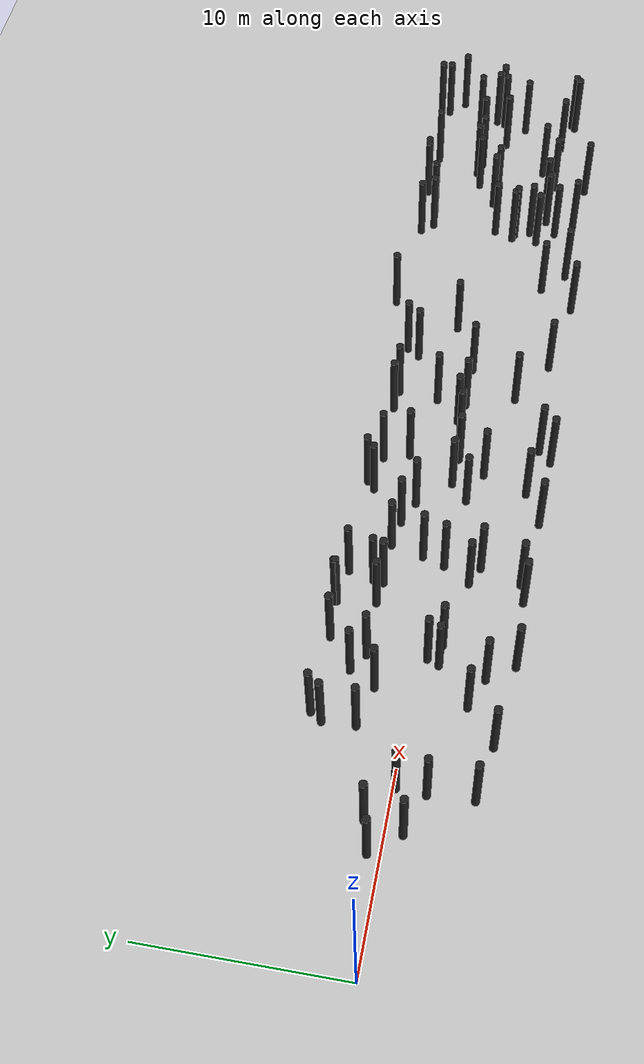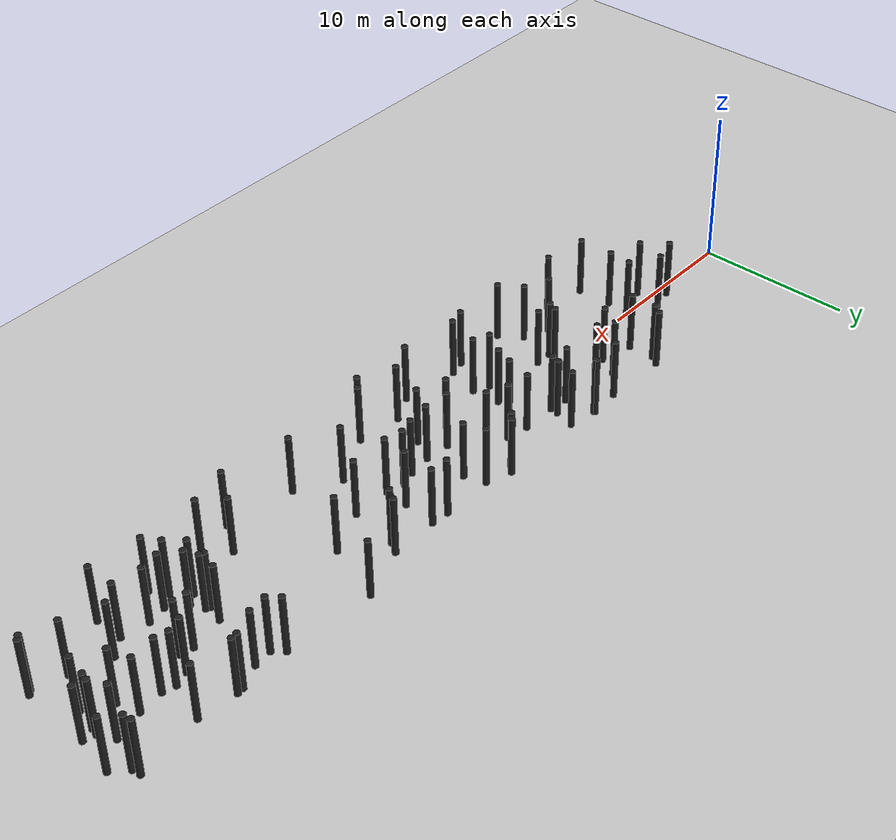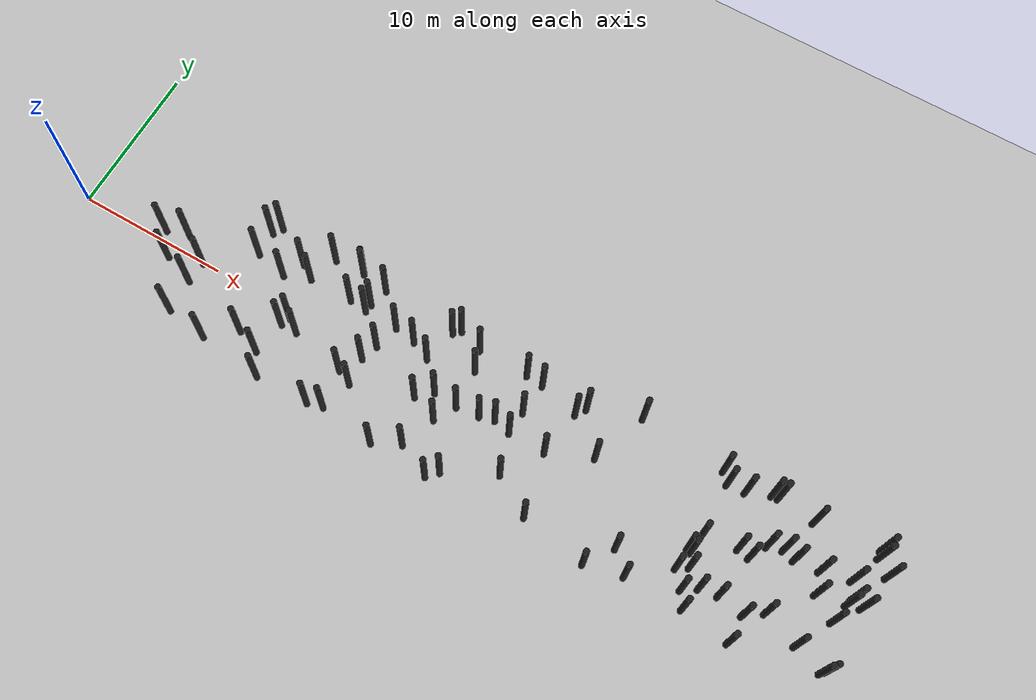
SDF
<sdf version="1.5">
 <world name="default">
  <plugin name="disable_physics" filename="libdisable_physics.so"/>
  <light name="sun" type="directional">
   <cast_shadows>0</cast_shadows>
   <pose>0 0 10 0 -0 0</pose>
   <diffuse>0.8 0.8 0.8 1</diffuse>
   <specular>0.2 0.2 0.2 1</specular>
   <attenuation>
    <range>1000</range>
    <constant>0.9</constant>
    <linear>0.01</linear>
    <quadratic>0.001</quadratic>
   </attenuation>
   <direction>-0.5 0.1 -0.9</direction>
  </light>
  <model name="ground_plane">
   <static>1</static>
   <link name="link">
    <collision name="collision">
     <geometry><plane><normal>0 0 1</normal><size>200 200</size></plane></geometry>
     <surface><friction><ode><mu>100</mu><mu2>50</mu2></ode></friction></surface>
    </collision>
    <visual name="visual">
     <cast_shadows>0</cast_shadows>
     <geometry><plane><normal>0 0 1</normal><size>200 200</size></plane></geometry>
     <material>
      <script><uri>file://media/materials/scripts/gazebo.material</uri><name>Gazebo/Grey</name></script>
     </material>
    </visual>
   </link>
  </model>
  <physics name="default_physics" default="0" type="ode">
   <max_step_size>0.001</max_step_size>
   <real_time_factor>1</real_time_factor>
   <real_time_update_rate>1000</real_time_update_rate>
   <gravity>0 0 -9.8</gravity>
   <magnetic_field>5.5645e-06 2.28758e-05 -4.23884e-05</magnetic_field>
  </physics>
  <scene><ambient>0.4 0.4 0.4 1</ambient><background>0.7 0.7 0.7 1</background><shadows>0</shadows></scene>
  <spherical_coordinates>
   <surface_model>EARTH_WGS84</surface_model>
   <latitude_deg>0</latitude_deg>
   <longitude_deg>0</longitude_deg>
   <elevation>0</elevation>
   <heading_deg>0</heading_deg>
  </spherical_coordinates>
  <model name="forest_clone_0">
   <pose>36.6186 1.15635 -0.002302 0 -0 0</pose>
   <static>1</static>
   <link name="cylinder::link">
    <inertial>
     <mass>1</mass>
     <inertia><ixx>0.083</ixx><ixy>0</ixy><ixz>0</ixz><iyy>0.083</iyy><iyz>0</iyz><izz>0.083</izz></inertia>
    </inertial>
    <collision name="collision">
     <geometry><cylinder><radius>0.2</radius><length>4</length></cylinder></geometry>
    </collision>
    <visual name="visual">
     <geometry><cylinder><radius>0.2</radius><length>4</length></cylinder></geometry>
     <material>
      <script><uri>file://media/materials/scripts/gazebo.material</uri><name>Gazebo/Black</name></script>
     </material>
    </visual>
    <pose>0 0 2 0 -0 0</pose>
   </link>
  </model>
  <model name="forest_clone_1">
   <pose>53.0873 -0.587766 0.001862 0 -0 0</pose>
   <static>1</static>
   <link name="cylinder::link">
    <inertial>
     <mass>1</mass>
     <inertia><ixx>0.083</ixx><ixy>0</ixy><ixz>0</ixz><iyy>0.083</iyy><iyz>0</iyz><izz>0.083</izz></inertia>
    </inertial>
    <collision name="collision">
     <geometry><cylinder><radius>0.2</radius><length>4</length></cylinder></geometry>
    </collision>
    <visual name="visual">
     <geometry><cylinder><radius>0.2</radius><length>4</length></cylinder></geometry>
     <material>
      <script><uri>file://media/materials/scripts/gazebo.material</uri><name>Gazebo/Black</name></script>
     </material>
    </visual>
    <pose>0 0 2 0 -0 0</pose>
   </link>
  </model>
  <model name="forest_clone_2">
   <pose>19.735 -4.62989 0.00488 0 -0 0</pose>
   <static>1</static>
   <link name="cylinder::link">
    <inertial>
     <mass>1</mass>
     <inertia><ixx>0.083</ixx><ixy>0</ixy><ixz>0</ixz><iyy>0.083</iyy><iyz>0</iyz><izz>0.083</izz></inertia>
    </inertial>
    <collision name="collision">
     <geometry><cylinder><radius>0.2</radius><length>4</length></cylinder></geometry>
    </collision>
    <visual name="visual">
     <geometry><cylinder><radius>0.2</radius><length>4</length></cylinder></geometry>
     <material>
      <script><uri>file://media/materials/scripts/gazebo.material</uri><name>Gazebo/Black</name></script>
     </material>
    </visual>
    <pose>0 0 2 0 -0 0</pose>
   </link>
  </model>
  <model name="forest_clone_3">
   <pose>23.3371 2.08051 -0.002989 0 -0 0</pose>
   <static>1</static>
   <link name="cylinder::link">
    <inertial>
     <mass>1</mass>
     <inertia><ixx>0.083</ixx><ixy>0</ixy><ixz>0</ixz><iyy>0.083</iyy><iyz>0</iyz><izz>0.083</izz></inertia>
    </inertial>
    <collision name="collision">
     <geometry><cylinder><radius>0.2</radius><length>4</length></cylinder></geometry>
    </collision>
    <visual name="visual">
     <geometry><cylinder><radius>0.2</radius><length>4</length></cylinder></geometry>
     <material>
      <script><uri>file://media/materials/scripts/gazebo.material</uri><name>Gazebo/Black</name></script>
     </material>
    </visual>
    <pose>0 0 2 0 -0 0</pose>
   </link>
  </model>
  <model name="forest_clone_4">
   <pose>53.9948 -3.33298 -0.002268 0 -0 0</pose>
   <static>1</static>
   <link name="cylinder::link">
    <inertial>
     <mass>1</mass>
     <inertia><ixx>0.083</ixx><ixy>0</ixy><ixz>0</ixz><iyy>0.083</iyy><iyz>0</iyz><izz>0.083</izz></inertia>
    </inertial>
    <collision name="collision">
     <geometry><cylinder><radius>0.2</radius><length>4</length></cylinder></geometry>
    </collision>
    <visual name="visual">
     <geometry><cylinder><radius>0.2</radius><length>4</length></cylinder></geometry>
     <material>
      <script><uri>file://media/materials/scripts/gazebo.material</uri><name>Gazebo/Black</name></script>
     </material>
    </visual>
    <pose>0 0 2 0 -0 0</pose>
   </link>
  </model>
  <model name="forest_clone_5">
   <pose>16.1395 -4.73642 -0.000165 0 -0 0</pose>
   <static>1</static>
   <link name="cylinder::link">
    <inertial>
     <mass>1</mass>
     <inertia><ixx>0.083</ixx><ixy>0</ixy><ixz>0</ixz><iyy>0.083</iyy><iyz>0</iyz><izz>0.083</izz></inertia>
    </inertial>
    <collision name="collision">
     <geometry><cylinder><radius>0.2</radius><length>4</length></cylinder></geometry>
    </collision>
    <visual name="visual">
     <geometry><cylinder><radius>0.2</radius><length>4</length></cylinder></geometry>
     <material>
      <script><uri>file://media/materials/scripts/gazebo.material</uri><name>Gazebo/Black</name></script>
     </material>
    </visual>
    <pose>0 0 2 0 -0 0</pose>
   </link>
  </model>
  <model name="forest_clone_6">
   <pose>27.5638 2.34565 -0.001375 0 -0 0</pose>
   <static>1</static>
   <link name="cylinder::link">
    <inertial>
     <mass>1</mass>
     <inertia><ixx>0.083</ixx><ixy>0</ixy><ixz>0</ixz><iyy>0.083</iyy><iyz>0</iyz><izz>0.083</izz></inertia>
    </inertial>
    <collision name="collision">
     <geometry><cylinder><radius>0.2</radius><length>4</length></cylinder></geometry>
    </collision>
    <visual name="visual">
     <geometry><cylinder><radius>0.2</radius><length>4</length></cylinder></geometry>
     <material>
      <script><uri>file://media/materials/scripts/gazebo.material</uri><name>Gazebo/Black</name></script>
     </material>
    </visual>
    <pose>0 0 2 0 -0 0</pose>
   </link>
  </model>
  <model name="forest_clone_7">
   <pose>6.86446 -0.829664 0.002199 0 -0 0</pose>
   <static>1</static>
   <link name="cylinder::link">
    <inertial>
     <mass>1</mass>
     <inertia><ixx>0.083</ixx><ixy>0</ixy><ixz>0</ixz><iyy>0.083</iyy><iyz>0</iyz><izz>0.083</izz></inertia>
    </inertial>
    <collision name="collision">
     <geometry><cylinder><radius>0.2</radius><length>4</length></cylinder></geometry>
    </collision>
    <visual name="visual">
     <geometry><cylinder><radius>0.2</radius><length>4</length></cylinder></geometry>
     <material>
      <script><uri>file://media/materials/scripts/gazebo.material</uri><name>Gazebo/Black</name></script>
     </material>
    </visual>
    <pose>0 0 2 0 -0 0</pose>
   </link>
  </model>
  <model name="forest_clone_8">
   <pose>54.2438 1.00165 -0.004068 0 -0 0</pose>
   <static>1</static>
   <link name="cylinder::link">
    <inertial>
     <mass>1</mass>
     <inertia><ixx>0.083</ixx><ixy>0</ixy><ixz>0</ixz><iyy>0.083</iyy><iyz>0</iyz><izz>0.083</izz></inertia>
    </inertial>
    <collision name="collision">
     <geometry><cylinder><radius>0.2</radius><length>4</length></cylinder></geometry>
    </collision>
    <visual name="visual">
     <geometry><cylinder><radius>0.2</radius><length>4</length></cylinder></geometry>
     <material>
      <script><uri>file://media/materials/scripts/gazebo.material</uri><name>Gazebo/Black</name></script>
     </material>
    </visual>
    <pose>0 0 2 0 -0 0</pose>
   </link>
  </model>
  <model name="forest_clone_9">
   <pose>11.6936 3.89703 -4e-05 0 -0 0</pose>
   <static>1</static>
   <link name="cylinder::link">
    <inertial>
     <mass>1</mass>
     <inertia><ixx>0.083</ixx><ixy>0</ixy><ixz>0</ixz><iyy>0.083</iyy><iyz>0</iyz><izz>0.083</izz></inertia>
    </inertial>
    <collision name="collision">
     <geometry><cylinder><radius>0.2</radius><length>4</length></cylinder></geometry>
    </collision>
    <visual name="visual">
     <geometry><cylinder><radius>0.2</radius><length>4</length></cylinder></geometry>
     <material>
      <script><uri>file://media/materials/scripts/gazebo.material</uri><name>Gazebo/Black</name></script>
     </material>
    </visual>
    <pose>0 0 2 0 -0 0</pose>
   </link>
  </model>
  <model name="forest_clone_10">
   <pose>26.1507 -0.118058 -0.000189 0 -0 0</pose>
   <static>1</static>
   <link name="cylinder::link">
    <inertial>
     <mass>1</mass>
     <inertia><ixx>0.083</ixx><ixy>0</ixy><ixz>0</ixz><iyy>0.083</iyy><iyz>0</iyz><izz>0.083</izz></inertia>
    </inertial>
    <collision name="collision">
     <geometry><cylinder><radius>0.2</radius><length>4</length></cylinder></geometry>
    </collision>
    <visual name="visual">
     <geometry><cylinder><radius>0.2</radius><length>4</length></cylinder></geometry>
     <material>
      <script><uri>file://media/materials/scripts/gazebo.material</uri><name>Gazebo/Black</name></script>
     </material>
    </visual>
    <pose>0 0 2 0 -0 0</pose>
   </link>
  </model>
  <model name="forest_clone_11">
   <pose>14.5857 3.06083 -0.000358 0 -0 0</pose>
   <static>1</static>
   <link name="cylinder::link">
    <inertial>
     <mass>1</mass>
     <inertia><ixx>0.083</ixx><ixy>0</ixy><ixz>0</ixz><iyy>0.083</iyy><iyz>0</iyz><izz>0.083</izz></inertia>
    </inertial>
    <collision name="collision">
     <geometry><cylinder><radius>0.2</radius><length>4</length></cylinder></geometry>
    </collision>
    <visual name="visual">
     <geometry><cylinder><radius>0.2</radius><length>4</length></cylinder></geometry>
     <material>
      <script><uri>file://media/materials/scripts/gazebo.material</uri><name>Gazebo/Black</name></script>
     </material>
    </visual>
    <pose>0 0 2 0 -0 0</pose>
   </link>
  </model>
  <model name="forest_clone_12">
   <pose>30.221 0.206009 -0.002528 0 -0 0</pose>
   <static>1</static>
   <link name="cylinder::link">
    <inertial>
     <mass>1</mass>
     <inertia><ixx>0.083</ixx><ixy>0</ixy><ixz>0</ixz><iyy>0.083</iyy><iyz>0</iyz><izz>0.083</izz></inertia>
    </inertial>
    <collision name="collision">
     <geometry><cylinder><radius>0.2</radius><length>4</length></cylinder></geometry>
    </collision>
    <visual name="visual">
     <geometry><cylinder><radius>0.2</radius><length>4</length></cylinder></geometry>
     <material>
      <script><uri>file://media/materials/scripts/gazebo.material</uri><name>Gazebo/Black</name></script>
     </material>
    </visual>
    <pose>0 0 2 0 -0 0</pose>
   </link>
  </model>
  <model name="forest_clone_13">
   <pose>27.7577 -0.246484 0.004658 0 -0 0</pose>
   <static>1</static>
   <link name="cylinder::link">
    <inertial>
     <mass>1</mass>
     <inertia><ixx>0.083</ixx><ixy>0</ixy><ixz>0</ixz><iyy>0.083</iyy><iyz>0</iyz><izz>0.083</izz></inertia>
    </inertial>
    <collision name="collision">
     <geometry><cylinder><radius>0.2</radius><length>4</length></cylinder></geometry>
    </collision>
    <visual name="visual">
     <geometry><cylinder><radius>0.2</radius><length>4</length></cylinder></geometry>
     <material>
      <script><uri>file://media/materials/scripts/gazebo.material</uri><name>Gazebo/Black</name></script>
     </material>
    </visual>
    <pose>0 0 2 0 -0 0</pose>
   </link>
  </model>
  <model name="forest_clone_14">
   <pose>12.0933 4.47642 0.003314 0 -0 0</pose>
   <static>1</static>
   <link name="cylinder::link">
    <inertial>
     <mass>1</mass>
     <inertia><ixx>0.083</ixx><ixy>0</ixy><ixz>0</ixz><iyy>0.083</iyy><iyz>0</iyz><izz>0.083</izz></inertia>
    </inertial>
    <collision name="collision">
     <geometry><cylinder><radius>0.2</radius><length>4</length></cylinder></geometry>
    </collision>
    <visual name="visual">
     <geometry><cylinder><radius>0.2</radius><length>4</length></cylinder></geometry>
     <material>
      <script><uri>file://media/materials/scripts/gazebo.material</uri><name>Gazebo/Black</name></script>
     </material>
    </visual>
    <pose>0 0 2 0 -0 0</pose>
   </link>
  </model>
  <model name="forest_clone_15">
   <pose>16.1999 4.34021 0.004076 0 -0 0</pose>
   <static>1</static>
   <link name="cylinder::link">
    <inertial>
     <mass>1</mass>
     <inertia><ixx>0.083</ixx><ixy>0</ixy><ixz>0</ixz><iyy>0.083</iyy><iyz>0</iyz><izz>0.083</izz></inertia>
    </inertial>
    <collision name="collision">
     <geometry><cylinder><radius>0.2</radius><length>4</length></cylinder></geometry>
    </collision>
    <visual name="visual">
     <geometry><cylinder><radius>0.2</radius><length>4</length></cylinder></geometry>
     <material>
      <script><uri>file://media/materials/scripts/gazebo.material</uri><name>Gazebo/Black</name></script>
     </material>
    </visual>
    <pose>0 0 2 0 -0 0</pose>
   </link>
  </model>
  <model name="forest_clone_16">
   <pose>47.9173 1.52354 -0.003943 0 -0 0</pose>
   <static>1</static>
   <link name="cylinder::link">
    <inertial>
     <mass>1</mass>
     <inertia><ixx>0.083</ixx><ixy>0</ixy><ixz>0</ixz><iyy>0.083</iyy><iyz>0</iyz><izz>0.083</izz></inertia>
    </inertial>
    <collision name="collision">
     <geometry><cylinder><radius>0.2</radius><length>4</length></cylinder></geometry>
    </collision>
    <visual name="visual">
     <geometry><cylinder><radius>0.2</radius><length>4</length></cylinder></geometry>
     <material>
      <script><uri>file://media/materials/scripts/gazebo.material</uri><name>Gazebo/Black</name></script>
     </material>
    </visual>
    <pose>0 0 2 0 -0 0</pose>
   </link>
  </model>
  <model name="forest_clone_17">
   <pose>51.2139 1.74782 0.00405 0 -0 0</pose>
   <static>1</static>
   <link name="cylinder::link">
    <inertial>
     <mass>1</mass>
     <inertia><ixx>0.083</ixx><ixy>0</ixy><ixz>0</ixz><iyy>0.083</iyy><iyz>0</iyz><izz>0.083</izz></inertia>
    </inertial>
    <collision name="collision">
     <geometry><cylinder><radius>0.2</radius><length>4</length></cylinder></geometry>
    </collision>
    <visual name="visual">
     <geometry><cylinder><radius>0.2</radius><length>4</length></cylinder></geometry>
     <material>
      <script><uri>file://media/materials/scripts/gazebo.material</uri><name>Gazebo/Black</name></script>
     </material>
    </visual>
    <pose>0 0 2 0 -0 0</pose>
   </link>
  </model>
  <model name="forest_clone_18">
   <pose>21.1371 -0.47592 -0.00285 0 -0 0</pose>
   <static>1</static>
   <link name="cylinder::link">
    <inertial>
     <mass>1</mass>
     <inertia><ixx>0.083</ixx><ixy>0</ixy><ixz>0</ixz><iyy>0.083</iyy><iyz>0</iyz><izz>0.083</izz></inertia>
    </inertial>
    <collision name="collision">
     <geometry><cylinder><radius>0.2</radius><length>4</length></cylinder></geometry>
    </collision>
    <visual name="visual">
     <geometry><cylinder><radius>0.2</radius><length>4</length></cylinder></geometry>
     <material>
      <script><uri>file://media/materials/scripts/gazebo.material</uri><name>Gazebo/Black</name></script>
     </material>
    </visual>
    <pose>0 0 2 0 -0 0</pose>
   </link>
  </model>
  <model name="forest_clone_19">
   <pose>46.7562 -2.54993 0.003689 0 -0 0</pose>
   <static>1</static>
   <link name="cylinder::link">
    <inertial>
     <mass>1</mass>
     <inertia><ixx>0.083</ixx><ixy>0</ixy><ixz>0</ixz><iyy>0.083</iyy><iyz>0</iyz><izz>0.083</izz></inertia>
    </inertial>
    <collision name="collision">
     <geometry><cylinder><radius>0.2</radius><length>4</length></cylinder></geometry>
    </collision>
    <visual name="visual">
     <geometry><cylinder><radius>0.2</radius><length>4</length></cylinder></geometry>
     <material>
      <script><uri>file://media/materials/scripts/gazebo.material</uri><name>Gazebo/Black</name></script>
     </material>
    </visual>
    <pose>0 0 2 0 -0 0</pose>
   </link>
  </model>
  <model name="forest_clone_20">
   <pose>26.1761 -3.96041 0.004466 0 -0 0</pose>
   <static>1</static>
   <link name="cylinder::link">
    <inertial>
     <mass>1</mass>
     <inertia><ixx>0.083</ixx><ixy>0</ixy><ixz>0</ixz><iyy>0.083</iyy><iyz>0</iyz><izz>0.083</izz></inertia>
    </inertial>
    <collision name="collision">
     <geometry><cylinder><radius>0.2</radius><length>4</length></cylinder></geometry>
    </collision>
    <visual name="visual">
     <geometry><cylinder><radius>0.2</radius><length>4</length></cylinder></geometry>
     <material>
      <script><uri>file://media/materials/scripts/gazebo.material</uri><name>Gazebo/Black</name></script>
     </material>
    </visual>
    <pose>0 0 2 0 -0 0</pose>
   </link>
  </model>
  <model name="forest_clone_21">
   <pose>44.7057 -3.31949 5.8e-05 0 -0 0</pose>
   <static>1</static>
   <link name="cylinder::link">
    <inertial>
     <mass>1</mass>
     <inertia><ixx>0.083</ixx><ixy>0</ixy><ixz>0</ixz><iyy>0.083</iyy><iyz>0</iyz><izz>0.083</izz></inertia>
    </inertial>
    <collision name="collision">
     <geometry><cylinder><radius>0.2</radius><length>4</length></cylinder></geometry>
    </collision>
    <visual name="visual">
     <geometry><cylinder><radius>0.2</radius><length>4</length></cylinder></geometry>
     <material>
      <script><uri>file://media/materials/scripts/gazebo.material</uri><name>Gazebo/Black</name></script>
     </material>
    </visual>
    <pose>0 0 2 0 -0 0</pose>
   </link>
  </model>
  <model name="forest_clone_22">
   <pose>44.1997 3.70877 0.002893 0 -0 0</pose>
   <static>1</static>
   <link name="cylinder::link">
    <inertial>
     <mass>1</mass>
     <inertia><ixx>0.083</ixx><ixy>0</ixy><ixz>0</ixz><iyy>0.083</iyy><iyz>0</iyz><izz>0.083</izz></inertia>
    </inertial>
    <collision name="collision">
     <geometry><cylinder><radius>0.2</radius><length>4</length></cylinder></geometry>
    </collision>
    <visual name="visual">
     <geometry><cylinder><radius>0.2</radius><length>4</length></cylinder></geometry>
     <material>
      <script><uri>file://media/materials/scripts/gazebo.material</uri><name>Gazebo/Black</name></script>
     </material>
    </visual>
    <pose>0 0 2 0 -0 0</pose>
   </link>
  </model>
  <model name="forest_clone_23">
   <pose>21.4987 0.655511 0.000589 0 -0 0</pose>
   <static>1</static>
   <link name="cylinder::link">
    <inertial>
     <mass>1</mass>
     <inertia><ixx>0.083</ixx><ixy>0</ixy><ixz>0</ixz><iyy>0.083</iyy><iyz>0</iyz><izz>0.083</izz></inertia>
    </inertial>
    <collision name="collision">
     <geometry><cylinder><radius>0.2</radius><length>4</length></cylinder></geometry>
    </collision>
    <visual name="visual">
     <geometry><cylinder><radius>0.2</radius><length>4</length></cylinder></geometry>
     <material>
      <script><uri>file://media/materials/scripts/gazebo.material</uri><name>Gazebo/Black</name></script>
     </material>
    </visual>
    <pose>0 0 2 0 -0 0</pose>
   </link>
  </model>
  <model name="forest_clone_24">
   <pose>48.4517 -4.68981 0.00207 0 -0 0</pose>
   <static>1</static>
   <link name="cylinder::link">
    <inertial>
     <mass>1</mass>
     <inertia><ixx>0.083</ixx><ixy>0</ixy><ixz>0</ixz><iyy>0.083</iyy><iyz>0</iyz><izz>0.083</izz></inertia>
    </inertial>
    <collision name="collision">
     <geometry><cylinder><radius>0.2</radius><length>4</length></cylinder></geometry>
    </collision>
    <visual name="visual">
     <geometry><cylinder><radius>0.2</radius><length>4</length></cylinder></geometry>
     <material>
      <script><uri>file://media/materials/scripts/gazebo.material</uri><name>Gazebo/Black</name></script>
     </material>
    </visual>
    <pose>0 0 2 0 -0 0</pose>
   </link>
  </model>
  <model name="forest_clone_25">
   <pose>19.6484 2.34191 0.000782 0 -0 0</pose>
   <static>1</static>
   <link name="cylinder::link">
    <inertial>
     <mass>1</mass>
     <inertia><ixx>0.083</ixx><ixy>0</ixy><ixz>0</ixz><iyy>0.083</iyy><iyz>0</iyz><izz>0.083</izz></inertia>
    </inertial>
    <collision name="collision">
     <geometry><cylinder><radius>0.2</radius><length>4</length></cylinder></geometry>
    </collision>
    <visual name="visual">
     <geometry><cylinder><radius>0.2</radius><length>4</length></cylinder></geometry>
     <material>
      <script><uri>file://media/materials/scripts/gazebo.material</uri><name>Gazebo/Black</name></script>
     </material>
    </visual>
    <pose>0 0 2 0 -0 0</pose>
   </link>
  </model>
  <model name="forest_clone_26">
   <pose>44.3149 0.095188 -0.002215 0 -0 0</pose>
   <static>1</static>
   <link name="cylinder::link">
    <inertial>
     <mass>1</mass>
     <inertia><ixx>0.083</ixx><ixy>0</ixy><ixz>0</ixz><iyy>0.083</iyy><iyz>0</iyz><izz>0.083</izz></inertia>
    </inertial>
    <collision name="collision">
     <geometry><cylinder><radius>0.2</radius><length>4</length></cylinder></geometry>
    </collision>
    <visual name="visual">
     <geometry><cylinder><radius>0.2</radius><length>4</length></cylinder></geometry>
     <material>
      <script><uri>file://media/materials/scripts/gazebo.material</uri><name>Gazebo/Black</name></script>
     </material>
    </visual>
    <pose>0 0 2 0 -0 0</pose>
   </link>
  </model>
  <model name="forest_clone_27">
   <pose>34.2549 2.97276 -0.001591 0 -0 0</pose>
   <static>1</static>
   <link name="cylinder::link">
    <inertial>
     <mass>1</mass>
     <inertia><ixx>0.083</ixx><ixy>0</ixy><ixz>0</ixz><iyy>0.083</iyy><iyz>0</iyz><izz>0.083</izz></inertia>
    </inertial>
    <collision name="collision">
     <geometry><cylinder><radius>0.2</radius><length>4</length></cylinder></geometry>
    </collision>
    <visual name="visual">
     <geometry><cylinder><radius>0.2</radius><length>4</length></cylinder></geometry>
     <material>
      <script><uri>file://media/materials/scripts/gazebo.material</uri><name>Gazebo/Black</name></script>
     </material>
    </visual>
    <pose>0 0 2 0 -0 0</pose>
   </link>
  </model>
  <model name="forest_clone_28">
   <pose>9.03167 -3.80021 -0.00308 0 -0 0</pose>
   <static>1</static>
   <link name="cylinder::link">
    <inertial>
     <mass>1</mass>
     <inertia><ixx>0.083</ixx><ixy>0</ixy><ixz>0</ixz><iyy>0.083</iyy><iyz>0</iyz><izz>0.083</izz></inertia>
    </inertial>
    <collision name="collision">
     <geometry><cylinder><radius>0.2</radius><length>4</length></cylinder></geometry>
    </collision>
    <visual name="visual">
     <geometry><cylinder><radius>0.2</radius><length>4</length></cylinder></geometry>
     <material>
      <script><uri>file://media/materials/scripts/gazebo.material</uri><name>Gazebo/Black</name></script>
     </material>
    </visual>
    <pose>0 0 2 0 -0 0</pose>
   </link>
  </model>
  <model name="forest_clone_29">
   <pose>24.4455 -4.84335 0.004124 0 -0 0</pose>
   <static>1</static>
   <link name="cylinder::link">
    <inertial>
     <mass>1</mass>
     <inertia><ixx>0.083</ixx><ixy>0</ixy><ixz>0</ixz><iyy>0.083</iyy><iyz>0</iyz><izz>0.083</izz></inertia>
    </inertial>
    <collision name="collision">
     <geometry><cylinder><radius>0.2</radius><length>4</length></cylinder></geometry>
    </collision>
    <visual name="visual">
     <geometry><cylinder><radius>0.2</radius><length>4</length></cylinder></geometry>
     <material>
      <script><uri>file://media/materials/scripts/gazebo.material</uri><name>Gazebo/Black</name></script>
     </material>
    </visual>
    <pose>0 0 2 0 -0 0</pose>
   </link>
  </model>
  <model name="forest_clone_30">
   <pose>53.7739 -3.54947 -0.000682 0 -0 0</pose>
   <static>1</static>
   <link name="cylinder::link">
    <inertial>
     <mass>1</mass>
     <inertia><ixx>0.083</ixx><ixy>0</ixy><ixz>0</ixz><iyy>0.083</iyy><iyz>0</iyz><izz>0.083</izz></inertia>
    </inertial>
    <collision name="collision">
     <geometry><cylinder><radius>0.2</radius><length>4</length></cylinder></geometry>
    </collision>
    <visual name="visual">
     <geometry><cylinder><radius>0.2</radius><length>4</length></cylinder></geometry>
     <material>
      <script><uri>file://media/materials/scripts/gazebo.material</uri><name>Gazebo/Black</name></script>
     </material>
    </visual>
    <pose>0 0 2 0 -0 0</pose>
   </link>
  </model>
  <model name="forest_clone_31">
   <pose>31.4471 1.48323 -0.003509 0 -0 0</pose>
   <static>1</static>
   <link name="cylinder::link">
    <inertial>
     <mass>1</mass>
     <inertia><ixx>0.083</ixx><ixy>0</ixy><ixz>0</ixz><iyy>0.083</iyy><iyz>0</iyz><izz>0.083</izz></inertia>
    </inertial>
    <collision name="collision">
     <geometry><cylinder><radius>0.2</radius><length>4</length></cylinder></geometry>
    </collision>
    <visual name="visual">
     <geometry><cylinder><radius>0.2</radius><length>4</length></cylinder></geometry>
     <material>
      <script><uri>file://media/materials/scripts/gazebo.material</uri><name>Gazebo/Black</name></script>
     </material>
    </visual>
    <pose>0 0 2 0 -0 0</pose>
   </link>
  </model>
  <model name="forest_clone_32">
   <pose>5.70693 0.6143 0.001264 0 -0 0</pose>
   <static>1</static>
   <link name="cylinder::link">
    <inertial>
     <mass>1</mass>
     <inertia><ixx>0.083</ixx><ixy>0</ixy><ixz>0</ixz><iyy>0.083</iyy><iyz>0</iyz><izz>0.083</izz></inertia>
    </inertial>
    <collision name="collision">
     <geometry><cylinder><radius>0.2</radius><length>4</length></cylinder></geometry>
    </collision>
    <visual name="visual">
     <geometry><cylinder><radius>0.2</radius><length>4</length></cylinder></geometry>
     <material>
      <script><uri>file://media/materials/scripts/gazebo.material</uri><name>Gazebo/Black</name></script>
     </material>
    </visual>
    <pose>0 0 2 0 -0 0</pose>
   </link>
  </model>
  <model name="forest_clone_33">
   <pose>48.8591 1.80171 0.003193 0 -0 0</pose>
   <static>1</static>
   <link name="cylinder::link">
    <inertial>
     <mass>1</mass>
     <inertia><ixx>0.083</ixx><ixy>0</ixy><ixz>0</ixz><iyy>0.083</iyy><iyz>0</iyz><izz>0.083</izz></inertia>
    </inertial>
    <collision name="collision">
     <geometry><cylinder><radius>0.2</radius><length>4</length></cylinder></geometry>
    </collision>
    <visual name="visual">
     <geometry><cylinder><radius>0.2</radius><length>4</length></cylinder></geometry>
     <material>
      <script><uri>file://media/materials/scripts/gazebo.material</uri><name>Gazebo/Black</name></script>
     </material>
    </visual>
    <pose>0 0 2 0 -0 0</pose>
   </link>
  </model>
  <model name="forest_clone_34">
   <pose>28.3636 -4.96296 -0.001198 0 -0 0</pose>
   <static>1</static>
   <link name="cylinder::link">
    <inertial>
     <mass>1</mass>
     <inertia><ixx>0.083</ixx><ixy>0</ixy><ixz>0</ixz><iyy>0.083</iyy><iyz>0</iyz><izz>0.083</izz></inertia>
    </inertial>
    <collision name="collision">
     <geometry><cylinder><radius>0.2</radius><length>4</length></cylinder></geometry>
    </collision>
    <visual name="visual">
     <geometry><cylinder><radius>0.2</radius><length>4</length></cylinder></geometry>
     <material>
      <script><uri>file://media/materials/scripts/gazebo.material</uri><name>Gazebo/Black</name></script>
     </material>
    </visual>
    <pose>0 0 2 0 -0 0</pose>
   </link>
  </model>
  <model name="forest_clone_35">
   <pose>18.1963 4.48754 -0.000638 0 -0 0</pose>
   <static>1</static>
   <link name="cylinder::link">
    <inertial>
     <mass>1</mass>
     <inertia><ixx>0.083</ixx><ixy>0</ixy><ixz>0</ixz><iyy>0.083</iyy><iyz>0</iyz><izz>0.083</izz></inertia>
    </inertial>
    <collision name="collision">
     <geometry><cylinder><radius>0.2</radius><length>4</length></cylinder></geometry>
    </collision>
    <visual name="visual">
     <geometry><cylinder><radius>0.2</radius><length>4</length></cylinder></geometry>
     <material>
      <script><uri>file://media/materials/scripts/gazebo.material</uri><name>Gazebo/Black</name></script>
     </material>
    </visual>
    <pose>0 0 2 0 -0 0</pose>
   </link>
  </model>
  <model name="forest_clone_36">
   <pose>20.7416 -4.36568 0.001531 0 -0 0</pose>
   <static>1</static>
   <link name="cylinder::link">
    <inertial>
     <mass>1</mass>
     <inertia><ixx>0.083</ixx><ixy>0</ixy><ixz>0</ixz><iyy>0.083</iyy><iyz>0</iyz><izz>0.083</izz></inertia>
    </inertial>
    <collision name="collision">
     <geometry><cylinder><radius>0.2</radius><length>4</length></cylinder></geometry>
    </collision>
    <visual name="visual">
     <geometry><cylinder><radius>0.2</radius><length>4</length></cylinder></geometry>
     <material>
      <script><uri>file://media/materials/scripts/gazebo.material</uri><name>Gazebo/Black</name></script>
     </material>
    </visual>
    <pose>0 0 2 0 -0 0</pose>
   </link>
  </model>
  <model name="forest_clone_37">
   <pose>43.8723 -2.33321 0.002737 0 -0 0</pose>
   <static>1</static>
   <link name="cylinder::link">
    <inertial>
     <mass>1</mass>
     <inertia><ixx>0.083</ixx><ixy>0</ixy><ixz>0</ixz><iyy>0.083</iyy><iyz>0</iyz><izz>0.083</izz></inertia>
    </inertial>
    <collision name="collision">
     <geometry><cylinder><radius>0.2</radius><length>4</length></cylinder></geometry>
    </collision>
    <visual name="visual">
     <geometry><cylinder><radius>0.2</radius><length>4</length></cylinder></geometry>
     <material>
      <script><uri>file://media/materials/scripts/gazebo.material</uri><name>Gazebo/Black</name></script>
     </material>
    </visual>
    <pose>0 0 2 0 -0 0</pose>
   </link>
  </model>
  <model name="forest_clone_38">
   <pose>15.5802 -1.07966 0.000842 0 -0 0</pose>
   <static>1</static>
   <link name="cylinder::link">
    <inertial>
     <mass>1</mass>
     <inertia><ixx>0.083</ixx><ixy>0</ixy><ixz>0</ixz><iyy>0.083</iyy><iyz>0</iyz><izz>0.083</izz></inertia>
    </inertial>
    <collision name="collision">
     <geometry><cylinder><radius>0.2</radius><length>4</length></cylinder></geometry>
    </collision>
    <visual name="visual">
     <geometry><cylinder><radius>0.2</radius><length>4</length></cylinder></geometry>
     <material>
      <script><uri>file://media/materials/scripts/gazebo.material</uri><name>Gazebo/Black</name></script>
     </material>
    </visual>
    <pose>0 0 2 0 -0 0</pose>
   </link>
  </model>
  <model name="forest_clone_39">
   <pose>13.8792 1.75486 -0.003355 0 -0 0</pose>
   <static>1</static>
   <link name="cylinder::link">
    <inertial>
     <mass>1</mass>
     <inertia><ixx>0.083</ixx><ixy>0</ixy><ixz>0</ixz><iyy>0.083</iyy><iyz>0</iyz><izz>0.083</izz></inertia>
    </inertial>
    <collision name="collision">
     <geometry><cylinder><radius>0.2</radius><length>4</length></cylinder></geometry>
    </collision>
    <visual name="visual">
     <geometry><cylinder><radius>0.2</radius><length>4</length></cylinder></geometry>
     <material>
      <script><uri>file://media/materials/scripts/gazebo.material</uri><name>Gazebo/Black</name></script>
     </material>
    </visual>
    <pose>0 0 2 0 -0 0</pose>
   </link>
  </model>
  <model name="forest_clone_40">
   <pose>45.5813 -2.73667 0.004571 0 -0 0</pose>
   <static>1</static>
   <link name="cylinder::link">
    <inertial>
     <mass>1</mass>
     <inertia><ixx>0.083</ixx><ixy>0</ixy><ixz>0</ixz><iyy>0.083</iyy><iyz>0</iyz><izz>0.083</izz></inertia>
    </inertial>
    <collision name="collision">
     <geometry><cylinder><radius>0.2</radius><length>4</length></cylinder></geometry>
    </collision>
    <visual name="visual">
     <geometry><cylinder><radius>0.2</radius><length>4</length></cylinder></geometry>
     <material>
      <script><uri>file://media/materials/scripts/gazebo.material</uri><name>Gazebo/Black</name></script>
     </material>
    </visual>
    <pose>0 0 2 0 -0 0</pose>
   </link>
  </model>
  <model name="forest_clone_41">
   <pose>49.5556 -2.06738 -0.004467 0 -0 0</pose>
   <static>1</static>
   <link name="cylinder::link">
    <inertial>
     <mass>1</mass>
     <inertia><ixx>0.083</ixx><ixy>0</ixy><ixz>0</ixz><iyy>0.083</iyy><iyz>0</iyz><izz>0.083</izz></inertia>
    </inertial>
    <collision name="collision">
     <geometry><cylinder><radius>0.2</radius><length>4</length></cylinder></geometry>
    </collision>
    <visual name="visual">
     <geometry><cylinder><radius>0.2</radius><length>4</length></cylinder></geometry>
     <material>
      <script><uri>file://media/materials/scripts/gazebo.material</uri><name>Gazebo/Black</name></script>
     </material>
    </visual>
    <pose>0 0 2 0 -0 0</pose>
   </link>
  </model>
  <model name="forest_clone_42">
   <pose>32.1973 -2.61731 -0.000572 0 -0 0</pose>
   <static>1</static>
   <link name="cylinder::link">
    <inertial>
     <mass>1</mass>
     <inertia><ixx>0.083</ixx><ixy>0</ixy><ixz>0</ixz><iyy>0.083</iyy><iyz>0</iyz><izz>0.083</izz></inertia>
    </inertial>
    <collision name="collision">
     <geometry><cylinder><radius>0.2</radius><length>4</length></cylinder></geometry>
    </collision>
    <visual name="visual">
     <geometry><cylinder><radius>0.2</radius><length>4</length></cylinder></geometry>
     <material>
      <script><uri>file://media/materials/scripts/gazebo.material</uri><name>Gazebo/Black</name></script>
     </material>
    </visual>
    <pose>0 0 2 0 -0 0</pose>
   </link>
  </model>
  <model name="forest_clone_43">
   <pose>26.9808 -1.64941 0.001403 0 -0 0</pose>
   <static>1</static>
   <link name="cylinder::link">
    <inertial>
     <mass>1</mass>
     <inertia><ixx>0.083</ixx><ixy>0</ixy><ixz>0</ixz><iyy>0.083</iyy><iyz>0</iyz><izz>0.083</izz></inertia>
    </inertial>
    <collision name="collision">
     <geometry><cylinder><radius>0.2</radius><length>4</length></cylinder></geometry>
    </collision>
    <visual name="visual">
     <geometry><cylinder><radius>0.2</radius><length>4</length></cylinder></geometry>
     <material>
      <script><uri>file://media/materials/scripts/gazebo.material</uri><name>Gazebo/Black</name></script>
     </material>
    </visual>
    <pose>0 0 2 0 -0 0</pose>
   </link>
  </model>
  <model name="forest_clone_44">
   <pose>8.92348 -1.56119 -0.003668 0 -0 0</pose>
   <static>1</static>
   <link name="cylinder::link">
    <inertial>
     <mass>1</mass>
     <inertia><ixx>0.083</ixx><ixy>0</ixy><ixz>0</ixz><iyy>0.083</iyy><iyz>0</iyz><izz>0.083</izz></inertia>
    </inertial>
    <collision name="collision">
     <geometry><cylinder><radius>0.2</radius><length>4</length></cylinder></geometry>
    </collision>
    <visual name="visual">
     <geometry><cylinder><radius>0.2</radius><length>4</length></cylinder></geometry>
     <material>
      <script><uri>file://media/materials/scripts/gazebo.material</uri><name>Gazebo/Black</name></script>
     </material>
    </visual>
    <pose>0 0 2 0 -0 0</pose>
   </link>
  </model>
  <model name="forest_clone_45">
   <pose>40.2809 -3.08541 0.000737 0 -0 0</pose>
   <static>1</static>
   <link name="cylinder::link">
    <inertial>
     <mass>1</mass>
     <inertia><ixx>0.083</ixx><ixy>0</ixy><ixz>0</ixz><iyy>0.083</iyy><iyz>0</iyz><izz>0.083</izz></inertia>
    </inertial>
    <collision name="collision">
     <geometry><cylinder><radius>0.2</radius><length>4</length></cylinder></geometry>
    </collision>
    <visual name="visual">
     <geometry><cylinder><radius>0.2</radius><length>4</length></cylinder></geometry>
     <material>
      <script><uri>file://media/materials/scripts/gazebo.material</uri><name>Gazebo/Black</name></script>
     </material>
    </visual>
    <pose>0 0 2 0 -0 0</pose>
   </link>
  </model>
  <model name="forest_clone_46">
   <pose>18.4556 2.47987 0.001708 0 -0 0</pose>
   <static>1</static>
   <link name="cylinder::link">
    <inertial>
     <mass>1</mass>
     <inertia><ixx>0.083</ixx><ixy>0</ixy><ixz>0</ixz><iyy>0.083</iyy><iyz>0</iyz><izz>0.083</izz></inertia>
    </inertial>
    <collision name="collision">
     <geometry><cylinder><radius>0.2</radius><length>4</length></cylinder></geometry>
    </collision>
    <visual name="visual">
     <geometry><cylinder><radius>0.2</radius><length>4</length></cylinder></geometry>
     <material>
      <script><uri>file://media/materials/scripts/gazebo.material</uri><name>Gazebo/Black</name></script>
     </material>
    </visual>
    <pose>0 0 2 0 -0 0</pose>
   </link>
  </model>
  <model name="forest_clone_47">
   <pose>46.8326 4.46381 -0.004421 0 -0 0</pose>
   <static>1</static>
   <link name="cylinder::link">
    <inertial>
     <mass>1</mass>
     <inertia><ixx>0.083</ixx><ixy>0</ixy><ixz>0</ixz><iyy>0.083</iyy><iyz>0</iyz><izz>0.083</izz></inertia>
    </inertial>
    <collision name="collision">
     <geometry><cylinder><radius>0.2</radius><length>4</length></cylinder></geometry>
    </collision>
    <visual name="visual">
     <geometry><cylinder><radius>0.2</radius><length>4</length></cylinder></geometry>
     <material>
      <script><uri>file://media/materials/scripts/gazebo.material</uri><name>Gazebo/Black</name></script>
     </material>
    </visual>
    <pose>0 0 2 0 -0 0</pose>
   </link>
  </model>
  <model name="forest_clone_48">
   <pose>25.12 3.80178 -0.002242 0 -0 0</pose>
   <static>1</static>
   <link name="cylinder::link">
    <inertial>
     <mass>1</mass>
     <inertia><ixx>0.083</ixx><ixy>0</ixy><ixz>0</ixz><iyy>0.083</iyy><iyz>0</iyz><izz>0.083</izz></inertia>
    </inertial>
    <collision name="collision">
     <geometry><cylinder><radius>0.2</radius><length>4</length></cylinder></geometry>
    </collision>
    <visual name="visual">
     <geometry><cylinder><radius>0.2</radius><length>4</length></cylinder></geometry>
     <material>
      <script><uri>file://media/materials/scripts/gazebo.material</uri><name>Gazebo/Black</name></script>
     </material>
    </visual>
    <pose>0 0 2 0 -0 0</pose>
   </link>
  </model>
  <model name="forest_clone_49">
   <pose>19.724 2.86631 0.003731 0 -0 0</pose>
   <static>1</static>
   <link name="cylinder::link">
    <inertial>
     <mass>1</mass>
     <inertia><ixx>0.083</ixx><ixy>0</ixy><ixz>0</ixz><iyy>0.083</iyy><iyz>0</iyz><izz>0.083</izz></inertia>
    </inertial>
    <collision name="collision">
     <geometry><cylinder><radius>0.2</radius><length>4</length></cylinder></geometry>
    </collision>
    <visual name="visual">
     <geometry><cylinder><radius>0.2</radius><length>4</length></cylinder></geometry>
     <material>
      <script><uri>file://media/materials/scripts/gazebo.material</uri><name>Gazebo/Black</name></script>
     </material>
    </visual>
    <pose>0 0 2 0 -0 0</pose>
   </link>
  </model>
  <model name="forest_clone_50">
   <pose>33.8144 -0.086384 -0.002482 0 -0 0</pose>
   <static>1</static>
   <link name="cylinder::link">
    <inertial>
     <mass>1</mass>
     <inertia><ixx>0.083</ixx><ixy>0</ixy><ixz>0</ixz><iyy>0.083</iyy><iyz>0</iyz><izz>0.083</izz></inertia>
    </inertial>
    <collision name="collision">
     <geometry><cylinder><radius>0.2</radius><length>4</length></cylinder></geometry>
    </collision>
    <visual name="visual">
     <geometry><cylinder><radius>0.2</radius><length>4</length></cylinder></geometry>
     <material>
      <script><uri>file://media/materials/scripts/gazebo.material</uri><name>Gazebo/Black</name></script>
     </material>
    </visual>
    <pose>0 0 2 0 -0 0</pose>
   </link>
  </model>
  <model name="forest_clone_51">
   <pose>27.1444 3.67133 0.003379 0 -0 0</pose>
   <static>1</static>
   <link name="cylinder::link">
    <inertial>
     <mass>1</mass>
     <inertia><ixx>0.083</ixx><ixy>0</ixy><ixz>0</ixz><iyy>0.083</iyy><iyz>0</iyz><izz>0.083</izz></inertia>
    </inertial>
    <collision name="collision">
     <geometry><cylinder><radius>0.2</radius><length>4</length></cylinder></geometry>
    </collision>
    <visual name="visual">
     <geometry><cylinder><radius>0.2</radius><length>4</length></cylinder></geometry>
     <material>
      <script><uri>file://media/materials/scripts/gazebo.material</uri><name>Gazebo/Black</name></script>
     </material>
    </visual>
    <pose>0 0 2 0 -0 0</pose>
   </link>
  </model>
  <model name="forest_clone_52">
   <pose>15.5269 2.43154 0.004404 0 -0 0</pose>
   <static>1</static>
   <link name="cylinder::link">
    <inertial>
     <mass>1</mass>
     <inertia><ixx>0.083</ixx><ixy>0</ixy><ixz>0</ixz><iyy>0.083</iyy><iyz>0</iyz><izz>0.083</izz></inertia>
    </inertial>
    <collision name="collision">
     <geometry><cylinder><radius>0.2</radius><length>4</length></cylinder></geometry>
    </collision>
    <visual name="visual">
     <geometry><cylinder><radius>0.2</radius><length>4</length></cylinder></geometry>
     <material>
      <script><uri>file://media/materials/scripts/gazebo.material</uri><name>Gazebo/Black</name></script>
     </material>
    </visual>
    <pose>0 0 2 0 -0 0</pose>
   </link>
  </model>
  <model name="forest_clone_53">
   <pose>18.2167 4.42349 0.003352 0 -0 0</pose>
   <static>1</static>
   <link name="cylinder::link">
    <inertial>
     <mass>1</mass>
     <inertia><ixx>0.083</ixx><ixy>0</ixy><ixz>0</ixz><iyy>0.083</iyy><iyz>0</iyz><izz>0.083</izz></inertia>
    </inertial>
    <collision name="collision">
     <geometry><cylinder><radius>0.2</radius><length>4</length></cylinder></geometry>
    </collision>
    <visual name="visual">
     <geometry><cylinder><radius>0.2</radius><length>4</length></cylinder></geometry>
     <material>
      <script><uri>file://media/materials/scripts/gazebo.material</uri><name>Gazebo/Black</name></script>
     </material>
    </visual>
    <pose>0 0 2 0 -0 0</pose>
   </link>
  </model>
  <model name="forest_clone_54">
   <pose>21.9007 2.3242 -0.004758 0 -0 0</pose>
   <static>1</static>
   <link name="cylinder::link">
    <inertial>
     <mass>1</mass>
     <inertia><ixx>0.083</ixx><ixy>0</ixy><ixz>0</ixz><iyy>0.083</iyy><iyz>0</iyz><izz>0.083</izz></inertia>
    </inertial>
    <collision name="collision">
     <geometry><cylinder><radius>0.2</radius><length>4</length></cylinder></geometry>
    </collision>
    <visual name="visual">
     <geometry><cylinder><radius>0.2</radius><length>4</length></cylinder></geometry>
     <material>
      <script><uri>file://media/materials/scripts/gazebo.material</uri><name>Gazebo/Black</name></script>
     </material>
    </visual>
    <pose>0 0 2 0 -0 0</pose>
   </link>
  </model>
  <model name="forest_clone_55">
   <pose>30.48 3.70209 -0.000585 0 -0 0</pose>
   <static>1</static>
   <link name="cylinder::link">
    <inertial>
     <mass>1</mass>
     <inertia><ixx>0.083</ixx><ixy>0</ixy><ixz>0</ixz><iyy>0.083</iyy><iyz>0</iyz><izz>0.083</izz></inertia>
    </inertial>
    <collision name="collision">
     <geometry><cylinder><radius>0.2</radius><length>4</length></cylinder></geometry>
    </collision>
    <visual name="visual">
     <geometry><cylinder><radius>0.2</radius><length>4</length></cylinder></geometry>
     <material>
      <script><uri>file://media/materials/scripts/gazebo.material</uri><name>Gazebo/Black</name></script>
     </material>
    </visual>
    <pose>0 0 2 0 -0 0</pose>
   </link>
  </model>
  <model name="forest_clone_56">
   <pose>29.2596 -0.061953 0.002523 0 -0 0</pose>
   <static>1</static>
   <link name="cylinder::link">
    <inertial>
     <mass>1</mass>
     <inertia><ixx>0.083</ixx><ixy>0</ixy><ixz>0</ixz><iyy>0.083</iyy><iyz>0</iyz><izz>0.083</izz></inertia>
    </inertial>
    <collision name="collision">
     <geometry><cylinder><radius>0.2</radius><length>4</length></cylinder></geometry>
    </collision>
    <visual name="visual">
     <geometry><cylinder><radius>0.2</radius><length>4</length></cylinder></geometry>
     <material>
      <script><uri>file://media/materials/scripts/gazebo.material</uri><name>Gazebo/Black</name></script>
     </material>
    </visual>
    <pose>0 0 2 0 -0 0</pose>
   </link>
  </model>
  <model name="forest_clone_57">
   <pose>11.8159 -4.24119 -0.00419 0 -0 0</pose>
   <static>1</static>
   <link name="cylinder::link">
    <inertial>
     <mass>1</mass>
     <inertia><ixx>0.083</ixx><ixy>0</ixy><ixz>0</ixz><iyy>0.083</iyy><iyz>0</iyz><izz>0.083</izz></inertia>
    </inertial>
    <collision name="collision">
     <geometry><cylinder><radius>0.2</radius><length>4</length></cylinder></geometry>
    </collision>
    <visual name="visual">
     <geometry><cylinder><radius>0.2</radius><length>4</length></cylinder></geometry>
     <material>
      <script><uri>file://media/materials/scripts/gazebo.material</uri><name>Gazebo/Black</name></script>
     </material>
    </visual>
    <pose>0 0 2 0 -0 0</pose>
   </link>
  </model>
  <model name="forest_clone_58">
   <pose>31.3579 -0.059241 -0.003216 0 -0 0</pose>
   <static>1</static>
   <link name="cylinder::link">
    <inertial>
     <mass>1</mass>
     <inertia><ixx>0.083</ixx><ixy>0</ixy><ixz>0</ixz><iyy>0.083</iyy><iyz>0</iyz><izz>0.083</izz></inertia>
    </inertial>
    <collision name="collision">
     <geometry><cylinder><radius>0.2</radius><length>4</length></cylinder></geometry>
    </collision>
    <visual name="visual">
     <geometry><cylinder><radius>0.2</radius><length>4</length></cylinder></geometry>
     <material>
      <script><uri>file://media/materials/scripts/gazebo.material</uri><name>Gazebo/Black</name></script>
     </material>
    </visual>
    <pose>0 0 2 0 -0 0</pose>
   </link>
  </model>
  <model name="forest_clone_59">
   <pose>9.00278 -0.105543 -0.004005 0 -0 0</pose>
   <static>1</static>
   <link name="cylinder::link">
    <inertial>
     <mass>1</mass>
     <inertia><ixx>0.083</ixx><ixy>0</ixy><ixz>0</ixz><iyy>0.083</iyy><iyz>0</iyz><izz>0.083</izz></inertia>
    </inertial>
    <collision name="collision">
     <geometry><cylinder><radius>0.2</radius><length>4</length></cylinder></geometry>
    </collision>
    <visual name="visual">
     <geometry><cylinder><radius>0.2</radius><length>4</length></cylinder></geometry>
     <material>
      <script><uri>file://media/materials/scripts/gazebo.material</uri><name>Gazebo/Black</name></script>
     </material>
    </visual>
    <pose>0 0 2 0 -0 0</pose>
   </link>
  </model>
  <model name="forest_clone_60">
   <pose>43.9522 -0.92737 -0.003387 0 -0 0</pose>
   <static>1</static>
   <link name="cylinder::link">
    <inertial>
     <mass>1</mass>
     <inertia><ixx>0.083</ixx><ixy>0</ixy><ixz>0</ixz><iyy>0.083</iyy><iyz>0</iyz><izz>0.083</izz></inertia>
    </inertial>
    <collision name="collision">
     <geometry><cylinder><radius>0.2</radius><length>4</length></cylinder></geometry>
    </collision>
    <visual name="visual">
     <geometry><cylinder><radius>0.2</radius><length>4</length></cylinder></geometry>
     <material>
      <script><uri>file://media/materials/scripts/gazebo.material</uri><name>Gazebo/Black</name></script>
     </material>
    </visual>
    <pose>0 0 2 0 -0 0</pose>
   </link>
  </model>
  <model name="forest_clone_61">
   <pose>41.5047 -4.29283 0.004625 0 -0 0</pose>
   <static>1</static>
   <link name="cylinder::link">
    <inertial>
     <mass>1</mass>
     <inertia><ixx>0.083</ixx><ixy>0</ixy><ixz>0</ixz><iyy>0.083</iyy><iyz>0</iyz><izz>0.083</izz></inertia>
    </inertial>
    <collision name="collision">
     <geometry><cylinder><radius>0.2</radius><length>4</length></cylinder></geometry>
    </collision>
    <visual name="visual">
     <geometry><cylinder><radius>0.2</radius><length>4</length></cylinder></geometry>
     <material>
      <script><uri>file://media/materials/scripts/gazebo.material</uri><name>Gazebo/Black</name></script>
     </material>
    </visual>
    <pose>0 0 2 0 -0 0</pose>
   </link>
  </model>
  <model name="forest_clone_62">
   <pose>48.4763 -2.86006 0.002774 0 -0 0</pose>
   <static>1</static>
   <link name="cylinder::link">
    <inertial>
     <mass>1</mass>
     <inertia><ixx>0.083</ixx><ixy>0</ixy><ixz>0</ixz><iyy>0.083</iyy><iyz>0</iyz><izz>0.083</izz></inertia>
    </inertial>
    <collision name="collision">
     <geometry><cylinder><radius>0.2</radius><length>4</length></cylinder></geometry>
    </collision>
    <visual name="visual">
     <geometry><cylinder><radius>0.2</radius><length>4</length></cylinder></geometry>
     <material>
      <script><uri>file://media/materials/scripts/gazebo.material</uri><name>Gazebo/Black</name></script>
     </material>
    </visual>
    <pose>0 0 2 0 -0 0</pose>
   </link>
  </model>
  <model name="forest_clone_63">
   <pose>16.6744 -1.09103 -0.000946 0 -0 0</pose>
   <static>1</static>
   <link name="cylinder::link">
    <inertial>
     <mass>1</mass>
     <inertia><ixx>0.083</ixx><ixy>0</ixy><ixz>0</ixz><iyy>0.083</iyy><iyz>0</iyz><izz>0.083</izz></inertia>
    </inertial>
    <collision name="collision">
     <geometry><cylinder><radius>0.2</radius><length>4</length></cylinder></geometry>
    </collision>
    <visual name="visual">
     <geometry><cylinder><radius>0.2</radius><length>4</length></cylinder></geometry>
     <material>
      <script><uri>file://media/materials/scripts/gazebo.material</uri><name>Gazebo/Black</name></script>
     </material>
    </visual>
    <pose>0 0 2 0 -0 0</pose>
   </link>
  </model>
  <model name="forest_clone_64">
   <pose>43.6472 4.35618 0.000734 0 -0 0</pose>
   <static>1</static>
   <link name="cylinder::link">
    <inertial>
     <mass>1</mass>
     <inertia><ixx>0.083</ixx><ixy>0</ixy><ixz>0</ixz><iyy>0.083</iyy><iyz>0</iyz><izz>0.083</izz></inertia>
    </inertial>
    <collision name="collision">
     <geometry><cylinder><radius>0.2</radius><length>4</length></cylinder></geometry>
    </collision>
    <visual name="visual">
     <geometry><cylinder><radius>0.2</radius><length>4</length></cylinder></geometry>
     <material>
      <script><uri>file://media/materials/scripts/gazebo.material</uri><name>Gazebo/Black</name></script>
     </material>
    </visual>
    <pose>0 0 2 0 -0 0</pose>
   </link>
  </model>
  <model name="forest_clone_65">
   <pose>45.3633 3.82373 0.00324 0 -0 0</pose>
   <static>1</static>
   <link name="cylinder::link">
    <inertial>
     <mass>1</mass>
     <inertia><ixx>0.083</ixx><ixy>0</ixy><ixz>0</ixz><iyy>0.083</iyy><iyz>0</iyz><izz>0.083</izz></inertia>
    </inertial>
    <collision name="collision">
     <geometry><cylinder><radius>0.2</radius><length>4</length></cylinder></geometry>
    </collision>
    <visual name="visual">
     <geometry><cylinder><radius>0.2</radius><length>4</length></cylinder></geometry>
     <material>
      <script><uri>file://media/materials/scripts/gazebo.material</uri><name>Gazebo/Black</name></script>
     </material>
    </visual>
    <pose>0 0 2 0 -0 0</pose>
   </link>
  </model>
  <model name="forest_clone_66">
   <pose>53.4038 0.754985 -0.004641 0 -0 0</pose>
   <static>1</static>
   <link name="cylinder::link">
    <inertial>
     <mass>1</mass>
     <inertia><ixx>0.083</ixx><ixy>0</ixy><ixz>0</ixz><iyy>0.083</iyy><iyz>0</iyz><izz>0.083</izz></inertia>
    </inertial>
    <collision name="collision">
     <geometry><cylinder><radius>0.2</radius><length>4</length></cylinder></geometry>
    </collision>
    <visual name="visual">
     <geometry><cylinder><radius>0.2</radius><length>4</length></cylinder></geometry>
     <material>
      <script><uri>file://media/materials/scripts/gazebo.material</uri><name>Gazebo/Black</name></script>
     </material>
    </visual>
    <pose>0 0 2 0 -0 0</pose>
   </link>
  </model>
  <model name="forest_clone_67">
   <pose>47.235 4.50455 -0.004643 0 -0 0</pose>
   <static>1</static>
   <link name="cylinder::link">
    <inertial>
     <mass>1</mass>
     <inertia><ixx>0.083</ixx><ixy>0</ixy><ixz>0</ixz><iyy>0.083</iyy><iyz>0</iyz><izz>0.083</izz></inertia>
    </inertial>
    <collision name="collision">
     <geometry><cylinder><radius>0.2</radius><length>4</length></cylinder></geometry>
    </collision>
    <visual name="visual">
     <geometry><cylinder><radius>0.2</radius><length>4</length></cylinder></geometry>
     <material>
      <script><uri>file://media/materials/scripts/gazebo.material</uri><name>Gazebo/Black</name></script>
     </material>
    </visual>
    <pose>0 0 2 0 -0 0</pose>
   </link>
  </model>
  <model name="forest_clone_68">
   <pose>29.0083 -4.30308 5.1e-05 0 -0 0</pose>
   <static>1</static>
   <link name="cylinder::link">
    <inertial>
     <mass>1</mass>
     <inertia><ixx>0.083</ixx><ixy>0</ixy><ixz>0</ixz><iyy>0.083</iyy><iyz>0</iyz><izz>0.083</izz></inertia>
    </inertial>
    <collision name="collision">
     <geometry><cylinder><radius>0.2</radius><length>4</length></cylinder></geometry>
    </collision>
    <visual name="visual">
     <geometry><cylinder><radius>0.2</radius><length>4</length></cylinder></geometry>
     <material>
      <script><uri>file://media/materials/scripts/gazebo.material</uri><name>Gazebo/Black</name></script>
     </material>
    </visual>
    <pose>0 0 2 0 -0 0</pose>
   </link>
  </model>
  <model name="forest_clone_69">
   <pose>34.6805 3.63474 0.002379 0 -0 0</pose>
   <static>1</static>
   <link name="cylinder::link">
    <inertial>
     <mass>1</mass>
     <inertia><ixx>0.083</ixx><ixy>0</ixy><ixz>0</ixz><iyy>0.083</iyy><iyz>0</iyz><izz>0.083</izz></inertia>
    </inertial>
    <collision name="collision">
     <geometry><cylinder><radius>0.2</radius><length>4</length></cylinder></geometry>
    </collision>
    <visual name="visual">
     <geometry><cylinder><radius>0.2</radius><length>4</length></cylinder></geometry>
     <material>
      <script><uri>file://media/materials/scripts/gazebo.material</uri><name>Gazebo/Black</name></script>
     </material>
    </visual>
    <pose>0 0 2 0 -0 0</pose>
   </link>
  </model>
  <model name="forest_clone_70">
   <pose>46.5162 0.523306 0.004149 0 -0 0</pose>
   <static>1</static>
   <link name="cylinder::link">
    <inertial>
     <mass>1</mass>
     <inertia><ixx>0.083</ixx><ixy>0</ixy><ixz>0</ixz><iyy>0.083</iyy><iyz>0</iyz><izz>0.083</izz></inertia>
    </inertial>
    <collision name="collision">
     <geometry><cylinder><radius>0.2</radius><length>4</length></cylinder></geometry>
    </collision>
    <visual name="visual">
     <geometry><cylinder><radius>0.2</radius><length>4</length></cylinder></geometry>
     <material>
      <script><uri>file://media/materials/scripts/gazebo.material</uri><name>Gazebo/Black</name></script>
     </material>
    </visual>
    <pose>0 0 2 0 -0 0</pose>
   </link>
  </model>
  <model name="forest_clone_71">
   <pose>24.6107 1.53569 0.000974 0 -0 0</pose>
   <static>1</static>
   <link name="cylinder::link">
    <inertial>
     <mass>1</mass>
     <inertia><ixx>0.083</ixx><ixy>0</ixy><ixz>0</ixz><iyy>0.083</iyy><iyz>0</iyz><izz>0.083</izz></inertia>
    </inertial>
    <collision name="collision">
     <geometry><cylinder><radius>0.2</radius><length>4</length></cylinder></geometry>
    </collision>
    <visual name="visual">
     <geometry><cylinder><radius>0.2</radius><length>4</length></cylinder></geometry>
     <material>
      <script><uri>file://media/materials/scripts/gazebo.material</uri><name>Gazebo/Black</name></script>
     </material>
    </visual>
    <pose>0 0 2 0 -0 0</pose>
   </link>
  </model>
  <model name="forest_clone_72">
   <pose>15.2101 -3.39108 -0.003527 0 -0 0</pose>
   <static>1</static>
   <link name="cylinder::link">
    <inertial>
     <mass>1</mass>
     <inertia><ixx>0.083</ixx><ixy>0</ixy><ixz>0</ixz><iyy>0.083</iyy><iyz>0</iyz><izz>0.083</izz></inertia>
    </inertial>
    <collision name="collision">
     <geometry><cylinder><radius>0.2</radius><length>4</length></cylinder></geometry>
    </collision>
    <visual name="visual">
     <geometry><cylinder><radius>0.2</radius><length>4</length></cylinder></geometry>
     <material>
      <script><uri>file://media/materials/scripts/gazebo.material</uri><name>Gazebo/Black</name></script>
     </material>
    </visual>
    <pose>0 0 2 0 -0 0</pose>
   </link>
  </model>
  <model name="forest_clone_73">
   <pose>53.8202 4.72353 0.002338 0 -0 0</pose>
   <static>1</static>
   <link name="cylinder::link">
    <inertial>
     <mass>1</mass>
     <inertia><ixx>0.083</ixx><ixy>0</ixy><ixz>0</ixz><iyy>0.083</iyy><iyz>0</iyz><izz>0.083</izz></inertia>
    </inertial>
    <collision name="collision">
     <geometry><cylinder><radius>0.2</radius><length>4</length></cylinder></geometry>
    </collision>
    <visual name="visual">
     <geometry><cylinder><radius>0.2</radius><length>4</length></cylinder></geometry>
     <material>
      <script><uri>file://media/materials/scripts/gazebo.material</uri><name>Gazebo/Black</name></script>
     </material>
    </visual>
    <pose>0 0 2 0 -0 0</pose>
   </link>
  </model>
  <model name="forest_clone_74">
   <pose>45.2868 -4.30182 0.004773 0 -0 0</pose>
   <static>1</static>
   <link name="cylinder::link">
    <inertial>
     <mass>1</mass>
     <inertia><ixx>0.083</ixx><ixy>0</ixy><ixz>0</ixz><iyy>0.083</iyy><iyz>0</iyz><izz>0.083</izz></inertia>
    </inertial>
    <collision name="collision">
     <geometry><cylinder><radius>0.2</radius><length>4</length></cylinder></geometry>
    </collision>
    <visual name="visual">
     <geometry><cylinder><radius>0.2</radius><length>4</length></cylinder></geometry>
     <material>
      <script><uri>file://media/materials/scripts/gazebo.material</uri><name>Gazebo/Black</name></script>
     </material>
    </visual>
    <pose>0 0 2 0 -0 0</pose>
   </link>
  </model>
  <model name="forest_clone_75">
   <pose>44.5516 -1.88915 -0.000411 0 -0 0</pose>
   <static>1</static>
   <link name="cylinder::link">
    <inertial>
     <mass>1</mass>
     <inertia><ixx>0.083</ixx><ixy>0</ixy><ixz>0</ixz><iyy>0.083</iyy><iyz>0</iyz><izz>0.083</izz></inertia>
    </inertial>
    <collision name="collision">
     <geometry><cylinder><radius>0.2</radius><length>4</length></cylinder></geometry>
    </collision>
    <visual name="visual">
     <geometry><cylinder><radius>0.2</radius><length>4</length></cylinder></geometry>
     <material>
      <script><uri>file://media/materials/scripts/gazebo.material</uri><name>Gazebo/Black</name></script>
     </material>
    </visual>
    <pose>0 0 2 0 -0 0</pose>
   </link>
  </model>
  <model name="forest_clone_76">
   <pose>15.8236 -0.483268 0.004695 0 -0 0</pose>
   <static>1</static>
   <link name="cylinder::link">
    <inertial>
     <mass>1</mass>
     <inertia><ixx>0.083</ixx><ixy>0</ixy><ixz>0</ixz><iyy>0.083</iyy><iyz>0</iyz><izz>0.083</izz></inertia>
    </inertial>
    <collision name="collision">
     <geometry><cylinder><radius>0.2</radius><length>4</length></cylinder></geometry>
    </collision>
    <visual name="visual">
     <geometry><cylinder><radius>0.2</radius><length>4</length></cylinder></geometry>
     <material>
      <script><uri>file://media/materials/scripts/gazebo.material</uri><name>Gazebo/Black</name></script>
     </material>
    </visual>
    <pose>0 0 2 0 -0 0</pose>
   </link>
  </model>
  <model name="forest_clone_77">
   <pose>7.24082 1.02738 0.002951 0 -0 0</pose>
   <static>1</static>
   <link name="cylinder::link">
    <inertial>
     <mass>1</mass>
     <inertia><ixx>0.083</ixx><ixy>0</ixy><ixz>0</ixz><iyy>0.083</iyy><iyz>0</iyz><izz>0.083</izz></inertia>
    </inertial>
    <collision name="collision">
     <geometry><cylinder><radius>0.2</radius><length>4</length></cylinder></geometry>
    </collision>
    <visual name="visual">
     <geometry><cylinder><radius>0.2</radius><length>4</length></cylinder></geometry>
     <material>
      <script><uri>file://media/materials/scripts/gazebo.material</uri><name>Gazebo/Black</name></script>
     </material>
    </visual>
    <pose>0 0 2 0 -0 0</pose>
   </link>
  </model>
  <model name="forest_clone_78">
   <pose>34.7166 -4.14216 0.002613 0 -0 0</pose>
   <static>1</static>
   <link name="cylinder::link">
    <inertial>
     <mass>1</mass>
     <inertia><ixx>0.083</ixx><ixy>0</ixy><ixz>0</ixz><iyy>0.083</iyy><iyz>0</iyz><izz>0.083</izz></inertia>
    </inertial>
    <collision name="collision">
     <geometry><cylinder><radius>0.2</radius><length>4</length></cylinder></geometry>
    </collision>
    <visual name="visual">
     <geometry><cylinder><radius>0.2</radius><length>4</length></cylinder></geometry>
     <material>
      <script><uri>file://media/materials/scripts/gazebo.material</uri><name>Gazebo/Black</name></script>
     </material>
    </visual>
    <pose>0 0 2 0 -0 0</pose>
   </link>
  </model>
  <model name="forest_clone_79">
   <pose>21.3211 -2.28981 6.5e-05 0 -0 0</pose>
   <static>1</static>
   <link name="cylinder::link">
    <inertial>
     <mass>1</mass>
     <inertia><ixx>0.083</ixx><ixy>0</ixy><ixz>0</ixz><iyy>0.083</iyy><iyz>0</iyz><izz>0.083</izz></inertia>
    </inertial>
    <collision name="collision">
     <geometry><cylinder><radius>0.2</radius><length>4</length></cylinder></geometry>
    </collision>
    <visual name="visual">
     <geometry><cylinder><radius>0.2</radius><length>4</length></cylinder></geometry>
     <material>
      <script><uri>file://media/materials/scripts/gazebo.material</uri><name>Gazebo/Black</name></script>
     </material>
    </visual>
    <pose>0 0 2 0 -0 0</pose>
   </link>
  </model>
  <model name="forest_clone_80">
   <pose>49.6781 4.21743 -0.002124 0 -0 0</pose>
   <static>1</static>
   <link name="cylinder::link">
    <inertial>
     <mass>1</mass>
     <inertia><ixx>0.083</ixx><ixy>0</ixy><ixz>0</ixz><iyy>0.083</iyy><iyz>0</iyz><izz>0.083</izz></inertia>
    </inertial>
    <collision name="collision">
     <geometry><cylinder><radius>0.2</radius><length>4</length></cylinder></geometry>
    </collision>
    <visual name="visual">
     <geometry><cylinder><radius>0.2</radius><length>4</length></cylinder></geometry>
     <material>
      <script><uri>file://media/materials/scripts/gazebo.material</uri><name>Gazebo/Black</name></script>
     </material>
    </visual>
    <pose>0 0 2 0 -0 0</pose>
   </link>
  </model>
  <model name="forest_clone_81">
   <pose>37.9332 4.83701 0.002574 0 -0 0</pose>
   <static>1</static>
   <link name="cylinder::link">
    <inertial>
     <mass>1</mass>
     <inertia><ixx>0.083</ixx><ixy>0</ixy><ixz>0</ixz><iyy>0.083</iyy><iyz>0</iyz><izz>0.083</izz></inertia>
    </inertial>
    <collision name="collision">
     <geometry><cylinder><radius>0.2</radius><length>4</length></cylinder></geometry>
    </collision>
    <visual name="visual">
     <geometry><cylinder><radius>0.2</radius><length>4</length></cylinder></geometry>
     <material>
      <script><uri>file://media/materials/scripts/gazebo.material</uri><name>Gazebo/Black</name></script>
     </material>
    </visual>
    <pose>0 0 2 0 -0 0</pose>
   </link>
  </model>
  <model name="forest_clone_82">
   <pose>53.0835 2.20043 -0.0026 0 -0 0</pose>
   <static>1</static>
   <link name="cylinder::link">
    <inertial>
     <mass>1</mass>
     <inertia><ixx>0.083</ixx><ixy>0</ixy><ixz>0</ixz><iyy>0.083</iyy><iyz>0</iyz><izz>0.083</izz></inertia>
    </inertial>
    <collision name="collision">
     <geometry><cylinder><radius>0.2</radius><length>4</length></cylinder></geometry>
    </collision>
    <visual name="visual">
     <geometry><cylinder><radius>0.2</radius><length>4</length></cylinder></geometry>
     <material>
      <script><uri>file://media/materials/scripts/gazebo.material</uri><name>Gazebo/Black</name></script>
     </material>
    </visual>
    <pose>0 0 2 0 -0 0</pose>
   </link>
  </model>
  <model name="forest_clone_83">
   <pose>31.6269 3.59525 -0.004327 0 -0 0</pose>
   <static>1</static>
   <link name="cylinder::link">
    <inertial>
     <mass>1</mass>
     <inertia><ixx>0.083</ixx><ixy>0</ixy><ixz>0</ixz><iyy>0.083</iyy><iyz>0</iyz><izz>0.083</izz></inertia>
    </inertial>
    <collision name="collision">
     <geometry><cylinder><radius>0.2</radius><length>4</length></cylinder></geometry>
    </collision>
    <visual name="visual">
     <geometry><cylinder><radius>0.2</radius><length>4</length></cylinder></geometry>
     <material>
      <script><uri>file://media/materials/scripts/gazebo.material</uri><name>Gazebo/Black</name></script>
     </material>
    </visual>
    <pose>0 0 2 0 -0 0</pose>
   </link>
  </model>
  <model name="forest_clone_84">
   <pose>13.6168 -2.75672 -0.000208 0 -0 0</pose>
   <static>1</static>
   <link name="cylinder::link">
    <inertial>
     <mass>1</mass>
     <inertia><ixx>0.083</ixx><ixy>0</ixy><ixz>0</ixz><iyy>0.083</iyy><iyz>0</iyz><izz>0.083</izz></inertia>
    </inertial>
    <collision name="collision">
     <geometry><cylinder><radius>0.2</radius><length>4</length></cylinder></geometry>
    </collision>
    <visual name="visual">
     <geometry><cylinder><radius>0.2</radius><length>4</length></cylinder></geometry>
     <material>
      <script><uri>file://media/materials/scripts/gazebo.material</uri><name>Gazebo/Black</name></script>
     </material>
    </visual>
    <pose>0 0 2 0 -0 0</pose>
   </link>
  </model>
  <model name="forest_clone_85">
   <pose>51.8541 -2.89589 -0.000297 0 -0 0</pose>
   <static>1</static>
   <link name="cylinder::link">
    <inertial>
     <mass>1</mass>
     <inertia><ixx>0.083</ixx><ixy>0</ixy><ixz>0</ixz><iyy>0.083</iyy><iyz>0</iyz><izz>0.083</izz></inertia>
    </inertial>
    <collision name="collision">
     <geometry><cylinder><radius>0.2</radius><length>4</length></cylinder></geometry>
    </collision>
    <visual name="visual">
     <geometry><cylinder><radius>0.2</radius><length>4</length></cylinder></geometry>
     <material>
      <script><uri>file://media/materials/scripts/gazebo.material</uri><name>Gazebo/Black</name></script>
     </material>
    </visual>
    <pose>0 0 2 0 -0 0</pose>
   </link>
  </model>
  <model name="forest_clone_86">
   <pose>51.591 0.399792 0.002104 0 -0 0</pose>
   <static>1</static>
   <link name="cylinder::link">
    <inertial>
     <mass>1</mass>
     <inertia><ixx>0.083</ixx><ixy>0</ixy><ixz>0</ixz><iyy>0.083</iyy><iyz>0</iyz><izz>0.083</izz></inertia>
    </inertial>
    <collision name="collision">
     <geometry><cylinder><radius>0.2</radius><length>4</length></cylinder></geometry>
    </collision>
    <visual name="visual">
     <geometry><cylinder><radius>0.2</radius><length>4</length></cylinder></geometry>
     <material>
      <script><uri>file://media/materials/scripts/gazebo.material</uri><name>Gazebo/Black</name></script>
     </material>
    </visual>
    <pose>0 0 2 0 -0 0</pose>
   </link>
  </model>
  <model name="forest_clone_87">
   <pose>49.6493 1.58354 0.000142 0 -0 0</pose>
   <static>1</static>
   <link name="cylinder::link">
    <inertial>
     <mass>1</mass>
     <inertia><ixx>0.083</ixx><ixy>0</ixy><ixz>0</ixz><iyy>0.083</iyy><iyz>0</iyz><izz>0.083</izz></inertia>
    </inertial>
    <collision name="collision">
     <geometry><cylinder><radius>0.2</radius><length>4</length></cylinder></geometry>
    </collision>
    <visual name="visual">
     <geometry><cylinder><radius>0.2</radius><length>4</length></cylinder></geometry>
     <material>
      <script><uri>file://media/materials/scripts/gazebo.material</uri><name>Gazebo/Black</name></script>
     </material>
    </visual>
    <pose>0 0 2 0 -0 0</pose>
   </link>
  </model>
  <model name="forest_clone_88">
   <pose>47.3095 0.372778 0.002643 0 -0 0</pose>
   <static>1</static>
   <link name="cylinder::link">
    <inertial>
     <mass>1</mass>
     <inertia><ixx>0.083</ixx><ixy>0</ixy><ixz>0</ixz><iyy>0.083</iyy><iyz>0</iyz><izz>0.083</izz></inertia>
    </inertial>
    <collision name="collision">
     <geometry><cylinder><radius>0.2</radius><length>4</length></cylinder></geometry>
    </collision>
    <visual name="visual">
     <geometry><cylinder><radius>0.2</radius><length>4</length></cylinder></geometry>
     <material>
      <script><uri>file://media/materials/scripts/gazebo.material</uri><name>Gazebo/Black</name></script>
     </material>
    </visual>
    <pose>0 0 2 0 -0 0</pose>
   </link>
  </model>
  <model name="forest_clone_89">
   <pose>25.2247 -0.981196 0.003075 0 -0 0</pose>
   <static>1</static>
   <link name="cylinder::link">
    <inertial>
     <mass>1</mass>
     <inertia><ixx>0.083</ixx><ixy>0</ixy><ixz>0</ixz><iyy>0.083</iyy><iyz>0</iyz><izz>0.083</izz></inertia>
    </inertial>
    <collision name="collision">
     <geometry><cylinder><radius>0.2</radius><length>4</length></cylinder></geometry>
    </collision>
    <visual name="visual">
     <geometry><cylinder><radius>0.2</radius><length>4</length></cylinder></geometry>
     <material>
      <script><uri>file://media/materials/scripts/gazebo.material</uri><name>Gazebo/Black</name></script>
     </material>
    </visual>
    <pose>0 0 2 0 -0 0</pose>
   </link>
  </model>
  <model name="forest_clone_90">
   <pose>39.0577 -4.88126 0.003825 0 -0 0</pose>
   <static>1</static>
   <link name="cylinder::link">
    <inertial>
     <mass>1</mass>
     <inertia><ixx>0.083</ixx><ixy>0</ixy><ixz>0</ixz><iyy>0.083</iyy><iyz>0</iyz><izz>0.083</izz></inertia>
    </inertial>
    <collision name="collision">
     <geometry><cylinder><radius>0.2</radius><length>4</length></cylinder></geometry>
    </collision>
    <visual name="visual">
     <geometry><cylinder><radius>0.2</radius><length>4</length></cylinder></geometry>
     <material>
      <script><uri>file://media/materials/scripts/gazebo.material</uri><name>Gazebo/Black</name></script>
     </material>
    </visual>
    <pose>0 0 2 0 -0 0</pose>
   </link>
  </model>
  <model name="forest_clone_91">
   <pose>11.7529 2.23478 -0.002557 0 -0 0</pose>
   <static>1</static>
   <link name="cylinder::link">
    <inertial>
     <mass>1</mass>
     <inertia><ixx>0.083</ixx><ixy>0</ixy><ixz>0</ixz><iyy>0.083</iyy><iyz>0</iyz><izz>0.083</izz></inertia>
    </inertial>
    <collision name="collision">
     <geometry><cylinder><radius>0.2</radius><length>4</length></cylinder></geometry>
    </collision>
    <visual name="visual">
     <geometry><cylinder><radius>0.2</radius><length>4</length></cylinder></geometry>
     <material>
      <script><uri>file://media/materials/scripts/gazebo.material</uri><name>Gazebo/Black</name></script>
     </material>
    </visual>
    <pose>0 0 2 0 -0 0</pose>
   </link>
  </model>
  <model name="forest_clone_92">
   <pose>54.7512 3.38015 0.004444 0 -0 0</pose>
   <static>1</static>
   <link name="cylinder::link">
    <inertial>
     <mass>1</mass>
     <inertia><ixx>0.083</ixx><ixy>0</ixy><ixz>0</ixz><iyy>0.083</iyy><iyz>0</iyz><izz>0.083</izz></inertia>
    </inertial>
    <collision name="collision">
     <geometry><cylinder><radius>0.2</radius><length>4</length></cylinder></geometry>
    </collision>
    <visual name="visual">
     <geometry><cylinder><radius>0.2</radius><length>4</length></cylinder></geometry>
     <material>
      <script><uri>file://media/materials/scripts/gazebo.material</uri><name>Gazebo/Black</name></script>
     </material>
    </visual>
    <pose>0 0 2 0 -0 0</pose>
   </link>
  </model>
  <model name="forest_clone_93">
   <pose>25.5449 4.19784 0.002981 0 -0 0</pose>
   <static>1</static>
   <link name="cylinder::link">
    <inertial>
     <mass>1</mass>
     <inertia><ixx>0.083</ixx><ixy>0</ixy><ixz>0</ixz><iyy>0.083</iyy><iyz>0</iyz><izz>0.083</izz></inertia>
    </inertial>
    <collision name="collision">
     <geometry><cylinder><radius>0.2</radius><length>4</length></cylinder></geometry>
    </collision>
    <visual name="visual">
     <geometry><cylinder><radius>0.2</radius><length>4</length></cylinder></geometry>
     <material>
      <script><uri>file://media/materials/scripts/gazebo.material</uri><name>Gazebo/Black</name></script>
     </material>
    </visual>
    <pose>0 0 2 0 -0 0</pose>
   </link>
  </model>
  <model name="forest_clone_94">
   <pose>44.2045 -1.05142 0.001948 0 -0 0</pose>
   <static>1</static>
   <link name="cylinder::link">
    <inertial>
     <mass>1</mass>
     <inertia><ixx>0.083</ixx><ixy>0</ixy><ixz>0</ixz><iyy>0.083</iyy><iyz>0</iyz><izz>0.083</izz></inertia>
    </inertial>
    <collision name="collision">
     <geometry><cylinder><radius>0.2</radius><length>4</length></cylinder></geometry>
    </collision>
    <visual name="visual">
     <geometry><cylinder><radius>0.2</radius><length>4</length></cylinder></geometry>
     <material>
      <script><uri>file://media/materials/scripts/gazebo.material</uri><name>Gazebo/Black</name></script>
     </material>
    </visual>
    <pose>0 0 2 0 -0 0</pose>
   </link>
  </model>
  <model name="forest_clone_96">
   <pose>53.5385 1.21424 0.003694 0 -0 0</pose>
   <static>1</static>
   <link name="cylinder::link">
    <inertial>
     <mass>1</mass>
     <inertia><ixx>0.083</ixx><ixy>0</ixy><ixz>0</ixz><iyy>0.083</iyy><iyz>0</iyz><izz>0.083</izz></inertia>
    </inertial>
    <collision name="collision">
     <geometry><cylinder><radius>0.2</radius><length>4</length></cylinder></geometry>
    </collision>
    <visual name="visual">
     <geometry><cylinder><radius>0.2</radius><length>4</length></cylinder></geometry>
     <material>
      <script><uri>file://media/materials/scripts/gazebo.material</uri><name>Gazebo/Black</name></script>
     </material>
    </visual>
    <pose>0 0 2 0 -0 0</pose>
   </link>
  </model>
  <model name="forest_clone_97">
   <pose>20.036 4.14583 0.003654 0 -0 0</pose>
   <static>1</static>
   <link name="cylinder::link">
    <inertial>
     <mass>1</mass>
     <inertia><ixx>0.083</ixx><ixy>0</ixy><ixz>0</ixz><iyy>0.083</iyy><iyz>0</iyz><izz>0.083</izz></inertia>
    </inertial>
    <collision name="collision">
     <geometry><cylinder><radius>0.2</radius><length>4</length></cylinder></geometry>
    </collision>
    <visual name="visual">
     <geometry><cylinder><radius>0.2</radius><length>4</length></cylinder></geometry>
     <material>
      <script><uri>file://media/materials/scripts/gazebo.material</uri><name>Gazebo/Black</name></script>
     </material>
    </visual>
    <pose>0 0 2 0 -0 0</pose>
   </link>
  </model>
  <model name="forest_clone_98">
   <pose>53.8851 4.22173 0.001656 0 -0 0</pose>
   <static>1</static>
   <link name="cylinder::link">
    <inertial>
     <mass>1</mass>
     <inertia><ixx>0.083</ixx><ixy>0</ixy><ixz>0</ixz><iyy>0.083</iyy><iyz>0</iyz><izz>0.083</izz></inertia>
    </inertial>
    <collision name="collision">
     <geometry><cylinder><radius>0.2</radius><length>4</length></cylinder></geometry>
    </collision>
    <visual name="visual">
     <geometry><cylinder><radius>0.2</radius><length>4</length></cylinder></geometry>
     <material>
      <script><uri>file://media/materials/scripts/gazebo.material</uri><name>Gazebo/Black</name></script>
     </material>
    </visual>
    <pose>0 0 2 0 -0 0</pose>
   </link>
  </model>
  <model name="forest_clone_99">
   <pose>20.3332 -1.84013 -0.001249 0 -0 0</pose>
   <static>1</static>
   <link name="cylinder::link">
    <inertial>
     <mass>1</mass>
     <inertia><ixx>0.083</ixx><ixy>0</ixy><ixz>0</ixz><iyy>0.083</iyy><iyz>0</iyz><izz>0.083</izz></inertia>
    </inertial>
    <collision name="collision">
     <geometry><cylinder><radius>0.2</radius><length>4</length></cylinder></geometry>
    </collision>
    <visual name="visual">
     <geometry><cylinder><radius>0.2</radius><length>4</length></cylinder></geometry>
     <material>
      <script><uri>file://media/materials/scripts/gazebo.material</uri><name>Gazebo/Black</name></script>
     </material>
    </visual>
    <pose>0 0 2 0 -0 0</pose>
   </link>
  </model>
 </world>
</sdf>
